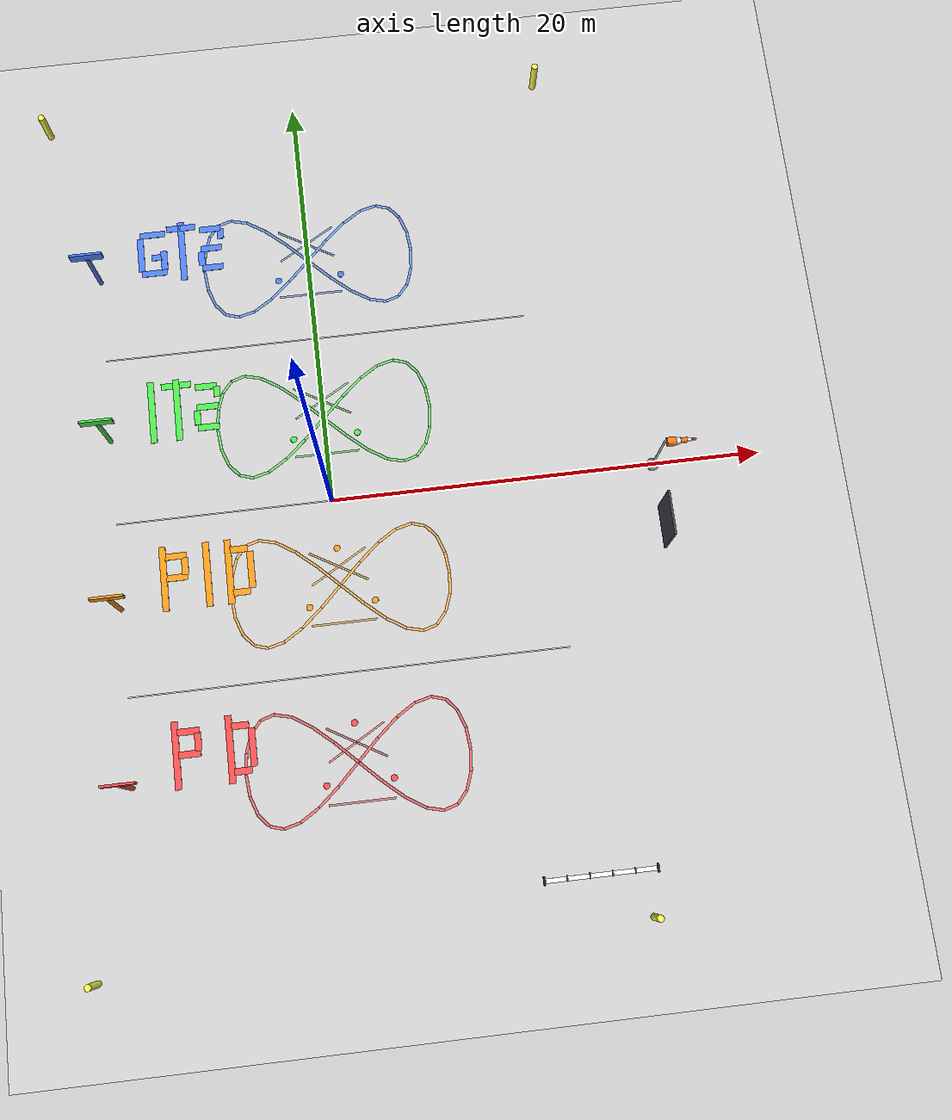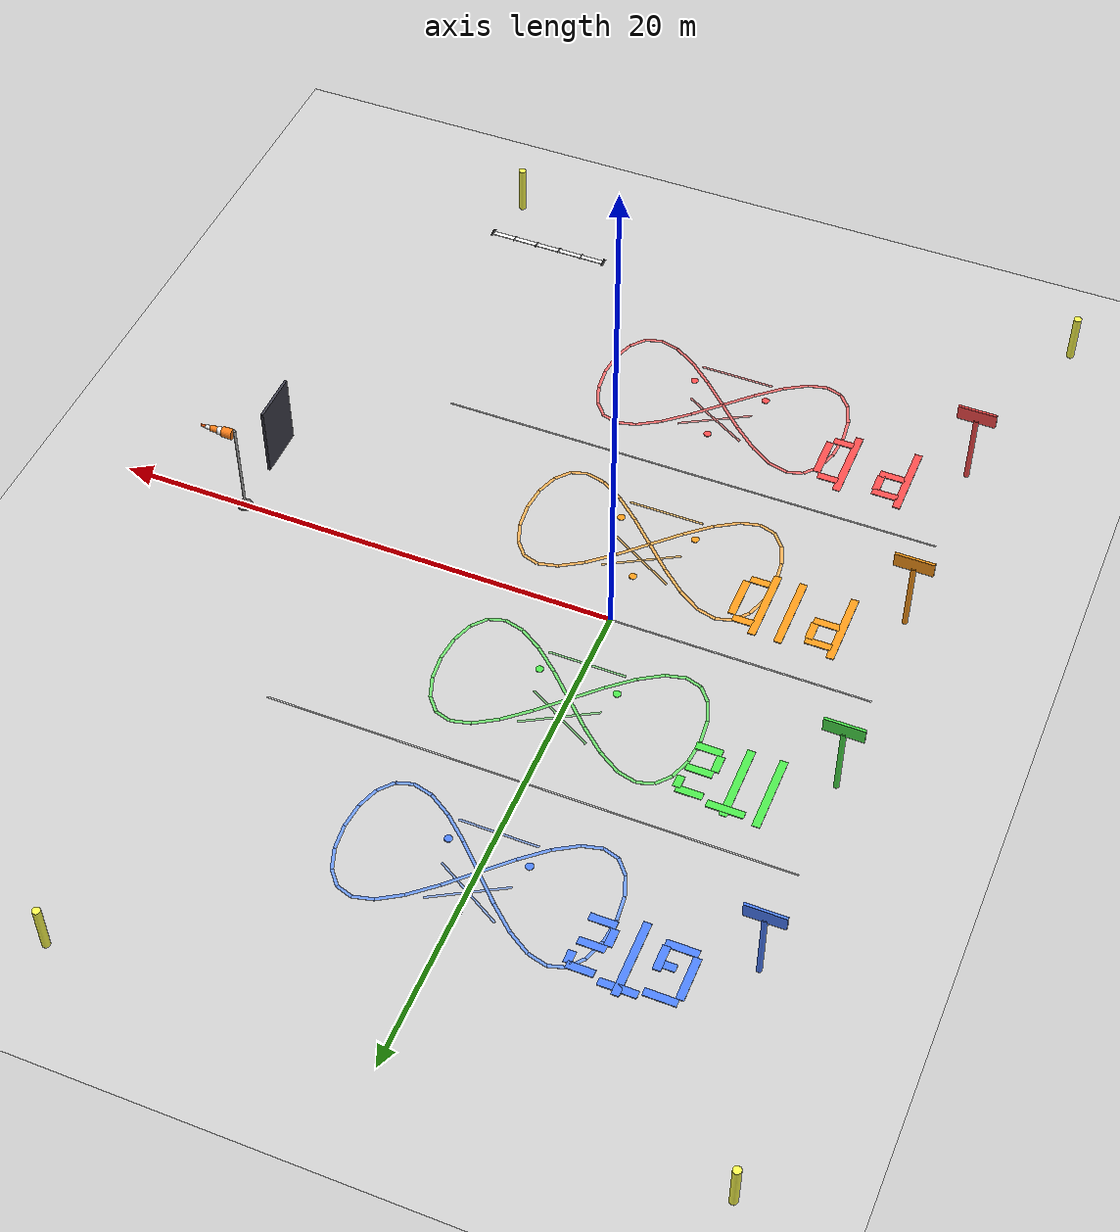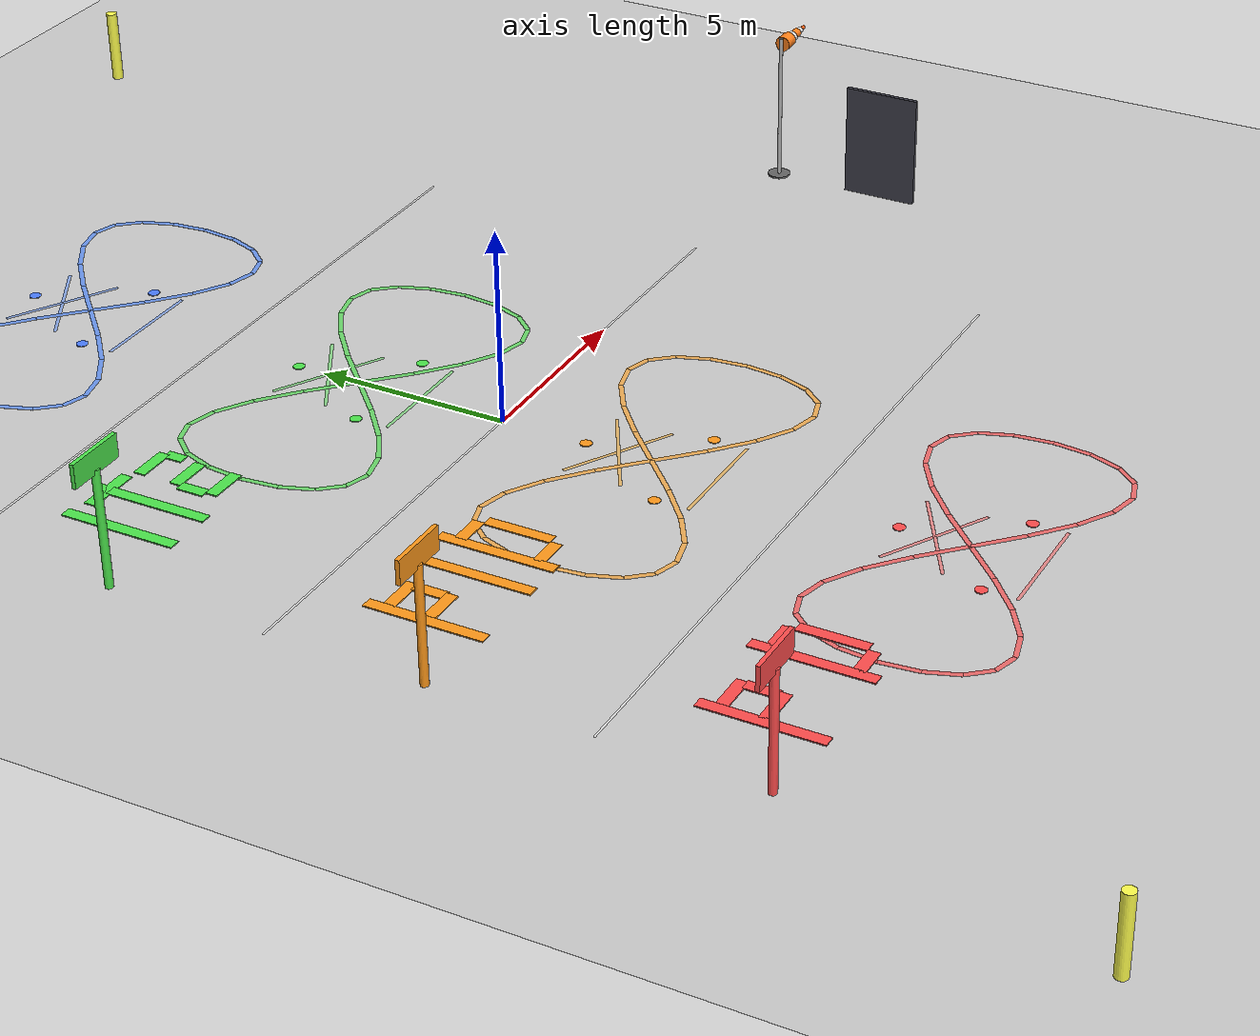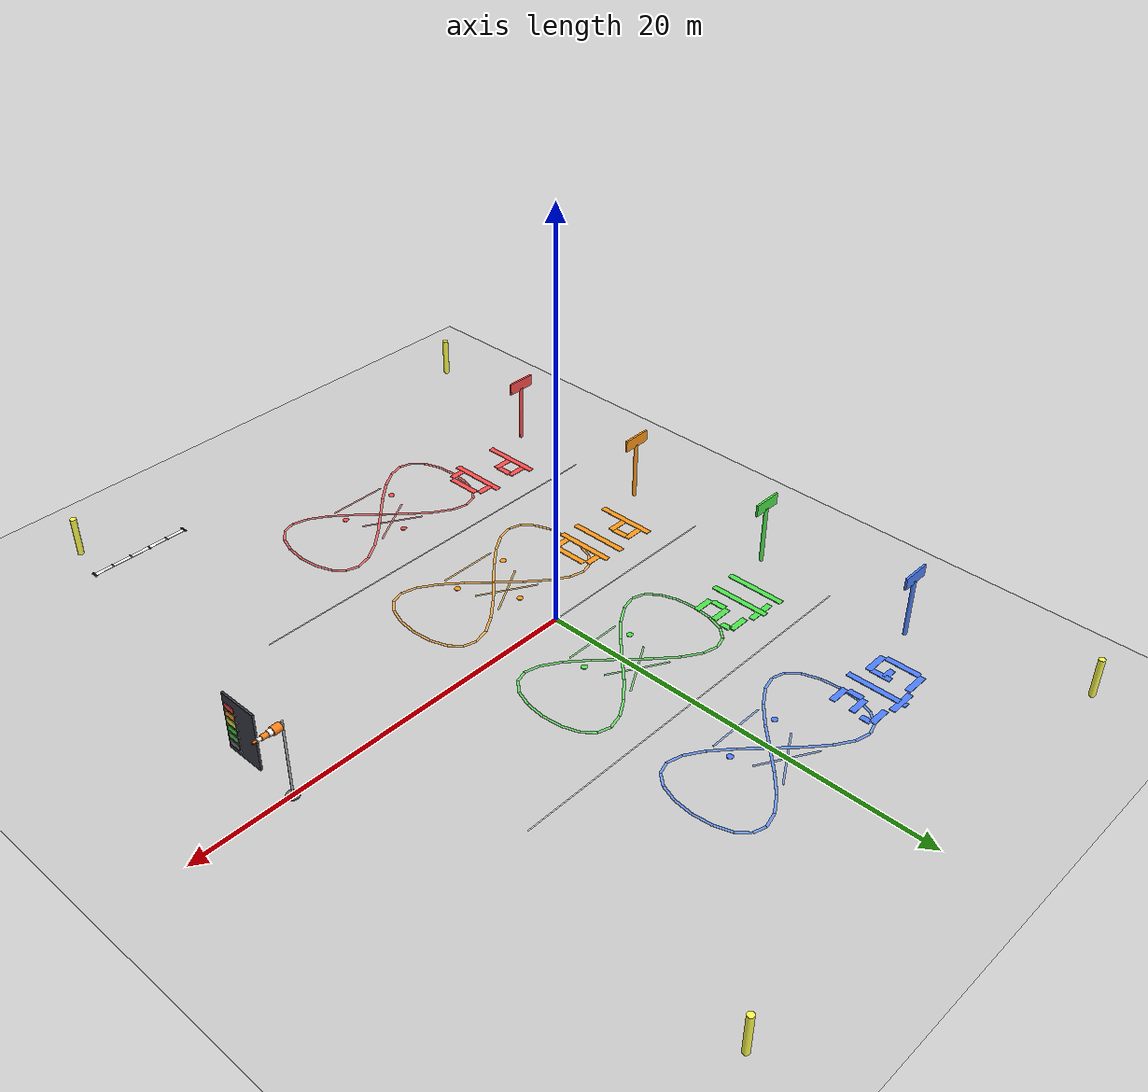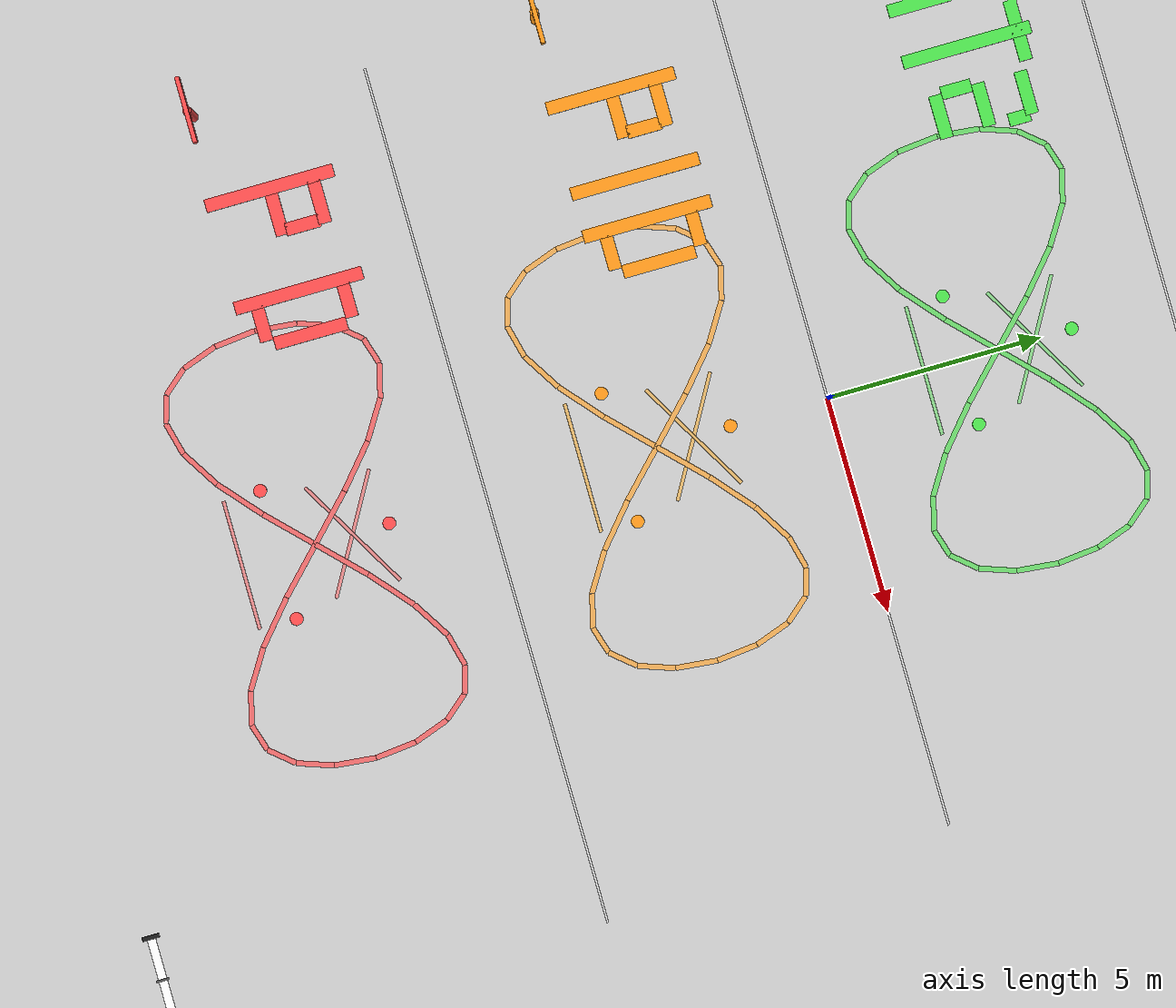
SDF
<sdf version="1.6">
 <world name="professional_formation_arena">
  <physics type="ode">
   <max_step_size>0.001</max_step_size>
   <real_time_factor>1.0</real_time_factor>
   <real_time_update_rate>1000</real_time_update_rate>
   <ode>
    <solver><type>quick</type><iters>50</iters><sor>1.3</sor></solver>
    <constraints>
     <cfm>0.0</cfm>
     <erp>0.2</erp>
     <contact_max_correcting_vel>100</contact_max_correcting_vel>
     <contact_surface_layer>0.001</contact_surface_layer>
    </constraints>
   </ode>
  </physics>
  <plugin name="gazebo_ros_init" filename="libgazebo_ros_init.so"><ros><namespace>/</namespace></ros></plugin>
  <plugin name="gazebo_ros_properties" filename="libgazebo_ros_properties.so">
   <ros><namespace>/</namespace></ros>
  </plugin>
  <light name="sun" type="directional">
   <pose>0 0 50 0 0 0</pose>
   <diffuse>0.9 0.9 0.9 1</diffuse>
   <specular>0.2 0.2 0.2 1</specular>
   <attenuation>
    <range>1000</range>
    <constant>0.9</constant>
    <linear>0.01</linear>
    <quadratic>0.001</quadratic>
   </attenuation>
   <direction>-0.3 0.4 -1.0</direction>
  </light>
  <light name="ambient" type="point">
   <pose>0 0 30 0 0 0</pose>
   <diffuse>0.3 0.3 0.35 1</diffuse>
   <specular>0.1 0.1 0.1 1</specular>
   <attenuation>
    <range>200</range>
    <constant>0.3</constant>
    <linear>0.01</linear>
    <quadratic>0.001</quadratic>
   </attenuation>
  </light>
  <scene><ambient>0.4 0.4 0.45 1</ambient><background>0.5 0.6 0.8 1</background><shadows>true</shadows></scene>
  <include><uri>model://arena_ground</uri></include>
  <model name="wind_indicator">
   <static>false</static>
   <pose>15 0 0 0 0 0</pose>
   <link name="base">
    <inertial>
     <mass>100</mass>
     <inertia><ixx>100</ixx><iyy>100</iyy><izz>100</izz><ixy>0</ixy><ixz>0</ixz><iyz>0</iyz></inertia>
    </inertial>
    <visual name="pole">
     <pose>0 0 2 0 0 0</pose>
     <geometry><cylinder><radius>0.05</radius><length>4.0</length></cylinder></geometry>
     <material><ambient>0.6 0.6 0.6 1</ambient><diffuse>0.7 0.7 0.7 1</diffuse></material>
    </visual>
    <visual name="base_plate">
     <pose>0 0 0.025 0 0 0</pose>
     <geometry><cylinder><radius>0.3</radius><length>0.05</length></cylinder></geometry>
     <material><ambient>0.3 0.3 0.3 1</ambient><diffuse>0.4 0.4 0.4 1</diffuse></material>
    </visual>
    <collision name="base_collision">
     <pose>0 0 0.025 0 0 0</pose>
     <geometry><cylinder><radius>0.3</radius><length>0.05</length></cylinder></geometry>
    </collision>
   </link>
   <link name="flag">
    <pose>0 0 3.8 0 0 0</pose>
    <inertial>
     <mass>0.5</mass>
     <inertia><ixx>0.01</ixx><iyy>0.1</iyy><izz>0.1</izz><ixy>0</ixy><ixz>0</ixz><iyz>0</iyz></inertia>
    </inertial>
    <visual name="sock_1">
     <pose>0.3 0 0 0 1.5708 0</pose>
     <geometry><cylinder><radius>0.2</radius><length>0.4</length></cylinder></geometry>
     <material><ambient>1 0.4 0 1</ambient><diffuse>1 0.5 0.1 1</diffuse></material>
    </visual>
    <visual name="sock_2">
     <pose>0.6 0 0 0 1.5708 0</pose>
     <geometry><cylinder><radius>0.15</radius><length>0.2</length></cylinder></geometry>
     <material><ambient>1 1 1 1</ambient><diffuse>1 1 1 1</diffuse></material>
    </visual>
    <visual name="sock_3">
     <pose>0.85 0 0 0 1.5708 0</pose>
     <geometry><cylinder><radius>0.12</radius><length>0.3</length></cylinder></geometry>
     <material><ambient>1 0.4 0 1</ambient><diffuse>1 0.5 0.1 1</diffuse></material>
    </visual>
    <visual name="sock_4">
     <pose>1.1 0 0 0 1.5708 0</pose>
     <geometry><cylinder><radius>0.08</radius><length>0.2</length></cylinder></geometry>
     <material><ambient>1 1 1 1</ambient><diffuse>1 1 1 1</diffuse></material>
    </visual>
    <visual name="sock_tip">
     <pose>1.3 0 0 0 1.5708 0</pose>
     <geometry><cylinder><radius>0.05</radius><length>0.2</length></cylinder></geometry>
     <material><ambient>1 0.3 0 1</ambient><diffuse>1 0.4 0.1 1</diffuse></material>
    </visual>
   </link>
   <joint name="flag_joint" type="revolute">
    <parent>base</parent>
    <child>flag</child>
    <axis>
     <xyz>0 0 1</xyz>
     <limit><lower>-3.15</lower><upper>3.15</upper></limit>
     <dynamics><damping>0.5</damping></dynamics>
    </axis>
   </joint>
   <plugin name="wind_flag_plugin" filename="libwind_flag_plugin.so">
    <joint_name>flag_joint</joint_name>
    <wind_topic>/wind/velocity</wind_topic>
    <update_rate>10</update_rate>
   </plugin>
  </model>
  <model name="traj_pd">
   <static>true</static>
   <link name="path">
    <visual name="seg0">
     <pose>0.488 -11.522 0.015 0 0 0.7757</pose>
     <geometry><box><size>1.366 0.12 0.015</size></box></geometry>
     <material><ambient>1 0.3 0.3 0.85</ambient><diffuse>1 0.4 0.4 0.85</diffuse></material>
    </visual>
    <visual name="seg1">
     <pose>1.444 -10.638 0.015 0 0 0.7130</pose>
     <geometry><box><size>1.240 0.12 0.015</size></box></geometry>
     <material><ambient>1 0.3 0.3 0.85</ambient><diffuse>1 0.4 0.4 0.85</diffuse></material>
    </visual>
    <visual name="seg2">
     <pose>2.346 -9.961 0.015 0 0 0.5600</pose>
     <geometry><box><size>1.020 0.12 0.015</size></box></geometry>
     <material><ambient>1 0.3 0.3 0.85</ambient><diffuse>1 0.4 0.4 0.85</diffuse></material>
    </visual>
    <visual name="seg3">
     <pose>3.157 -9.595 0.015 0 0 0.2461</pose>
     <geometry><box><size>0.781 0.12 0.015</size></box></geometry>
     <material><ambient>1 0.3 0.3 0.85</ambient><diffuse>1 0.4 0.4 0.85</diffuse></material>
    </visual>
    <visual name="seg4">
     <pose>3.846 -9.595 0.015 0 0 -0.2970</pose>
     <geometry><box><size>0.650 0.12 0.015</size></box></geometry>
     <material><ambient>1 0.3 0.3 0.85</ambient><diffuse>1 0.4 0.4 0.85</diffuse></material>
    </visual>
    <visual name="seg5">
     <pose>4.388 -9.961 0.015 0 0 -0.8648</pose>
     <geometry><box><size>0.712 0.12 0.015</size></box></geometry>
     <material><ambient>1 0.3 0.3 0.85</ambient><diffuse>1 0.4 0.4 0.85</diffuse></material>
    </visual>
    <visual name="seg6">
     <pose>4.762 -10.638 0.015 0 0 -1.2334</pose>
     <geometry><box><size>0.860 0.12 0.015</size></box></geometry>
     <material><ambient>1 0.3 0.3 0.85</ambient><diffuse>1 0.4 0.4 0.85</diffuse></material>
    </visual>
    <visual name="seg7">
     <pose>4.952 -11.522 0.015 0 0 -1.4707</pose>
     <geometry><box><size>0.962 0.12 0.015</size></box></geometry>
     <material><ambient>1 0.3 0.3 0.85</ambient><diffuse>1 0.4 0.4 0.85</diffuse></material>
    </visual>
    <visual name="seg8">
     <pose>4.952 -12.478 0.015 0 0 -1.6709</pose>
     <geometry><box><size>0.962 0.12 0.015</size></box></geometry>
     <material><ambient>1 0.3 0.3 0.85</ambient><diffuse>1 0.4 0.4 0.85</diffuse></material>
    </visual>
    <visual name="seg9">
     <pose>4.762 -13.362 0.015 0 0 -1.9082</pose>
     <geometry><box><size>0.860 0.12 0.015</size></box></geometry>
     <material><ambient>1 0.3 0.3 0.85</ambient><diffuse>1 0.4 0.4 0.85</diffuse></material>
    </visual>
    <visual name="seg10">
     <pose>4.388 -14.039 0.015 0 0 -2.2768</pose>
     <geometry><box><size>0.712 0.12 0.015</size></box></geometry>
     <material><ambient>1 0.3 0.3 0.85</ambient><diffuse>1 0.4 0.4 0.85</diffuse></material>
    </visual>
    <visual name="seg11">
     <pose>3.846 -14.405 0.015 0 0 -2.8446</pose>
     <geometry><box><size>0.650 0.12 0.015</size></box></geometry>
     <material><ambient>1 0.3 0.3 0.85</ambient><diffuse>1 0.4 0.4 0.85</diffuse></material>
    </visual>
    <visual name="seg12">
     <pose>3.157 -14.405 0.015 0 0 2.8955</pose>
     <geometry><box><size>0.781 0.12 0.015</size></box></geometry>
     <material><ambient>1 0.3 0.3 0.85</ambient><diffuse>1 0.4 0.4 0.85</diffuse></material>
    </visual>
    <visual name="seg13">
     <pose>2.346 -14.039 0.015 0 0 2.5816</pose>
     <geometry><box><size>1.020 0.12 0.015</size></box></geometry>
     <material><ambient>1 0.3 0.3 0.85</ambient><diffuse>1 0.4 0.4 0.85</diffuse></material>
    </visual>
    <visual name="seg14">
     <pose>1.444 -13.362 0.015 0 0 2.4286</pose>
     <geometry><box><size>1.240 0.12 0.015</size></box></geometry>
     <material><ambient>1 0.3 0.3 0.85</ambient><diffuse>1 0.4 0.4 0.85</diffuse></material>
    </visual>
    <visual name="seg15">
     <pose>0.488 -12.478 0.015 0 0 2.3659</pose>
     <geometry><box><size>1.366 0.12 0.015</size></box></geometry>
     <material><ambient>1 0.3 0.3 0.85</ambient><diffuse>1 0.4 0.4 0.85</diffuse></material>
    </visual>
    <visual name="seg16">
     <pose>-0.488 -11.522 0.015 0 0 2.3659</pose>
     <geometry><box><size>1.366 0.12 0.015</size></box></geometry>
     <material><ambient>1 0.3 0.3 0.85</ambient><diffuse>1 0.4 0.4 0.85</diffuse></material>
    </visual>
    <visual name="seg17">
     <pose>-1.444 -10.638 0.015 0 0 2.4286</pose>
     <geometry><box><size>1.240 0.12 0.015</size></box></geometry>
     <material><ambient>1 0.3 0.3 0.85</ambient><diffuse>1 0.4 0.4 0.85</diffuse></material>
    </visual>
    <visual name="seg18">
     <pose>-2.346 -9.961 0.015 0 0 2.5816</pose>
     <geometry><box><size>1.020 0.12 0.015</size></box></geometry>
     <material><ambient>1 0.3 0.3 0.85</ambient><diffuse>1 0.4 0.4 0.85</diffuse></material>
    </visual>
    <visual name="seg19">
     <pose>-3.157 -9.595 0.015 0 0 2.8955</pose>
     <geometry><box><size>0.781 0.12 0.015</size></box></geometry>
     <material><ambient>1 0.3 0.3 0.85</ambient><diffuse>1 0.4 0.4 0.85</diffuse></material>
    </visual>
    <visual name="seg20">
     <pose>-3.846 -9.595 0.015 0 0 -2.8446</pose>
     <geometry><box><size>0.650 0.12 0.015</size></box></geometry>
     <material><ambient>1 0.3 0.3 0.85</ambient><diffuse>1 0.4 0.4 0.85</diffuse></material>
    </visual>
    <visual name="seg21">
     <pose>-4.388 -9.961 0.015 0 0 -2.2768</pose>
     <geometry><box><size>0.712 0.12 0.015</size></box></geometry>
     <material><ambient>1 0.3 0.3 0.85</ambient><diffuse>1 0.4 0.4 0.85</diffuse></material>
    </visual>
    <visual name="seg22">
     <pose>-4.762 -10.638 0.015 0 0 -1.9082</pose>
     <geometry><box><size>0.860 0.12 0.015</size></box></geometry>
     <material><ambient>1 0.3 0.3 0.85</ambient><diffuse>1 0.4 0.4 0.85</diffuse></material>
    </visual>
    <visual name="seg23">
     <pose>-4.952 -11.522 0.015 0 0 -1.6709</pose>
     <geometry><box><size>0.962 0.12 0.015</size></box></geometry>
     <material><ambient>1 0.3 0.3 0.85</ambient><diffuse>1 0.4 0.4 0.85</diffuse></material>
    </visual>
    <visual name="seg24">
     <pose>-4.952 -12.478 0.015 0 0 -1.4707</pose>
     <geometry><box><size>0.962 0.12 0.015</size></box></geometry>
     <material><ambient>1 0.3 0.3 0.85</ambient><diffuse>1 0.4 0.4 0.85</diffuse></material>
    </visual>
    <visual name="seg25">
     <pose>-4.762 -13.362 0.015 0 0 -1.2334</pose>
     <geometry><box><size>0.860 0.12 0.015</size></box></geometry>
     <material><ambient>1 0.3 0.3 0.85</ambient><diffuse>1 0.4 0.4 0.85</diffuse></material>
    </visual>
    <visual name="seg26">
     <pose>-4.388 -14.039 0.015 0 0 -0.8648</pose>
     <geometry><box><size>0.712 0.12 0.015</size></box></geometry>
     <material><ambient>1 0.3 0.3 0.85</ambient><diffuse>1 0.4 0.4 0.85</diffuse></material>
    </visual>
    <visual name="seg27">
     <pose>-3.846 -14.405 0.015 0 0 -0.2970</pose>
     <geometry><box><size>0.650 0.12 0.015</size></box></geometry>
     <material><ambient>1 0.3 0.3 0.85</ambient><diffuse>1 0.4 0.4 0.85</diffuse></material>
    </visual>
    <visual name="seg28">
     <pose>-3.157 -14.405 0.015 0 0 0.2461</pose>
     <geometry><box><size>0.781 0.12 0.015</size></box></geometry>
     <material><ambient>1 0.3 0.3 0.85</ambient><diffuse>1 0.4 0.4 0.85</diffuse></material>
    </visual>
    <visual name="seg29">
     <pose>-2.346 -14.039 0.015 0 0 0.5600</pose>
     <geometry><box><size>1.020 0.12 0.015</size></box></geometry>
     <material><ambient>1 0.3 0.3 0.85</ambient><diffuse>1 0.4 0.4 0.85</diffuse></material>
    </visual>
    <visual name="seg30">
     <pose>-1.444 -13.362 0.015 0 0 0.7130</pose>
     <geometry><box><size>1.240 0.12 0.015</size></box></geometry>
     <material><ambient>1 0.3 0.3 0.85</ambient><diffuse>1 0.4 0.4 0.85</diffuse></material>
    </visual>
    <visual name="seg31">
     <pose>-0.488 -12.478 0.015 0 0 0.7757</pose>
     <geometry><box><size>1.366 0.12 0.015</size></box></geometry>
     <material><ambient>1 0.3 0.3 0.85</ambient><diffuse>1 0.4 0.4 0.85</diffuse></material>
    </visual>
   </link>
  </model>
  <model name="traj_pid">
   <static>true</static>
   <link name="path">
    <visual name="seg0">
     <pose>0.488 -3.522 0.015 0 0 0.7757</pose>
     <geometry><box><size>1.366 0.12 0.015</size></box></geometry>
     <material><ambient>1 0.6 0.2 0.85</ambient><diffuse>1 0.7 0.3 0.85</diffuse></material>
    </visual>
    <visual name="seg1">
     <pose>1.444 -2.638 0.015 0 0 0.7130</pose>
     <geometry><box><size>1.240 0.12 0.015</size></box></geometry>
     <material><ambient>1 0.6 0.2 0.85</ambient><diffuse>1 0.7 0.3 0.85</diffuse></material>
    </visual>
    <visual name="seg2">
     <pose>2.346 -1.961 0.015 0 0 0.5600</pose>
     <geometry><box><size>1.020 0.12 0.015</size></box></geometry>
     <material><ambient>1 0.6 0.2 0.85</ambient><diffuse>1 0.7 0.3 0.85</diffuse></material>
    </visual>
    <visual name="seg3">
     <pose>3.157 -1.595 0.015 0 0 0.2461</pose>
     <geometry><box><size>0.781 0.12 0.015</size></box></geometry>
     <material><ambient>1 0.6 0.2 0.85</ambient><diffuse>1 0.7 0.3 0.85</diffuse></material>
    </visual>
    <visual name="seg4">
     <pose>3.846 -1.595 0.015 0 0 -0.2970</pose>
     <geometry><box><size>0.650 0.12 0.015</size></box></geometry>
     <material><ambient>1 0.6 0.2 0.85</ambient><diffuse>1 0.7 0.3 0.85</diffuse></material>
    </visual>
    <visual name="seg5">
     <pose>4.388 -1.961 0.015 0 0 -0.8648</pose>
     <geometry><box><size>0.712 0.12 0.015</size></box></geometry>
     <material><ambient>1 0.6 0.2 0.85</ambient><diffuse>1 0.7 0.3 0.85</diffuse></material>
    </visual>
    <visual name="seg6">
     <pose>4.762 -2.638 0.015 0 0 -1.2334</pose>
     <geometry><box><size>0.860 0.12 0.015</size></box></geometry>
     <material><ambient>1 0.6 0.2 0.85</ambient><diffuse>1 0.7 0.3 0.85</diffuse></material>
    </visual>
    <visual name="seg7">
     <pose>4.952 -3.522 0.015 0 0 -1.4707</pose>
     <geometry><box><size>0.962 0.12 0.015</size></box></geometry>
     <material><ambient>1 0.6 0.2 0.85</ambient><diffuse>1 0.7 0.3 0.85</diffuse></material>
    </visual>
    <visual name="seg8">
     <pose>4.952 -4.478 0.015 0 0 -1.6709</pose>
     <geometry><box><size>0.962 0.12 0.015</size></box></geometry>
     <material><ambient>1 0.6 0.2 0.85</ambient><diffuse>1 0.7 0.3 0.85</diffuse></material>
    </visual>
    <visual name="seg9">
     <pose>4.762 -5.362 0.015 0 0 -1.9082</pose>
     <geometry><box><size>0.860 0.12 0.015</size></box></geometry>
     <material><ambient>1 0.6 0.2 0.85</ambient><diffuse>1 0.7 0.3 0.85</diffuse></material>
    </visual>
    <visual name="seg10">
     <pose>4.388 -6.039 0.015 0 0 -2.2768</pose>
     <geometry><box><size>0.712 0.12 0.015</size></box></geometry>
     <material><ambient>1 0.6 0.2 0.85</ambient><diffuse>1 0.7 0.3 0.85</diffuse></material>
    </visual>
    <visual name="seg11">
     <pose>3.846 -6.405 0.015 0 0 -2.8446</pose>
     <geometry><box><size>0.650 0.12 0.015</size></box></geometry>
     <material><ambient>1 0.6 0.2 0.85</ambient><diffuse>1 0.7 0.3 0.85</diffuse></material>
    </visual>
    <visual name="seg12">
     <pose>3.157 -6.405 0.015 0 0 2.8955</pose>
     <geometry><box><size>0.781 0.12 0.015</size></box></geometry>
     <material><ambient>1 0.6 0.2 0.85</ambient><diffuse>1 0.7 0.3 0.85</diffuse></material>
    </visual>
    <visual name="seg13">
     <pose>2.346 -6.039 0.015 0 0 2.5816</pose>
     <geometry><box><size>1.020 0.12 0.015</size></box></geometry>
     <material><ambient>1 0.6 0.2 0.85</ambient><diffuse>1 0.7 0.3 0.85</diffuse></material>
    </visual>
    <visual name="seg14">
     <pose>1.444 -5.362 0.015 0 0 2.4286</pose>
     <geometry><box><size>1.240 0.12 0.015</size></box></geometry>
     <material><ambient>1 0.6 0.2 0.85</ambient><diffuse>1 0.7 0.3 0.85</diffuse></material>
    </visual>
    <visual name="seg15">
     <pose>0.488 -4.478 0.015 0 0 2.3659</pose>
     <geometry><box><size>1.366 0.12 0.015</size></box></geometry>
     <material><ambient>1 0.6 0.2 0.85</ambient><diffuse>1 0.7 0.3 0.85</diffuse></material>
    </visual>
    <visual name="seg16">
     <pose>-0.488 -3.522 0.015 0 0 2.3659</pose>
     <geometry><box><size>1.366 0.12 0.015</size></box></geometry>
     <material><ambient>1 0.6 0.2 0.85</ambient><diffuse>1 0.7 0.3 0.85</diffuse></material>
    </visual>
    <visual name="seg17">
     <pose>-1.444 -2.638 0.015 0 0 2.4286</pose>
     <geometry><box><size>1.240 0.12 0.015</size></box></geometry>
     <material><ambient>1 0.6 0.2 0.85</ambient><diffuse>1 0.7 0.3 0.85</diffuse></material>
    </visual>
    <visual name="seg18">
     <pose>-2.346 -1.961 0.015 0 0 2.5816</pose>
     <geometry><box><size>1.020 0.12 0.015</size></box></geometry>
     <material><ambient>1 0.6 0.2 0.85</ambient><diffuse>1 0.7 0.3 0.85</diffuse></material>
    </visual>
    <visual name="seg19">
     <pose>-3.157 -1.595 0.015 0 0 2.8955</pose>
     <geometry><box><size>0.781 0.12 0.015</size></box></geometry>
     <material><ambient>1 0.6 0.2 0.85</ambient><diffuse>1 0.7 0.3 0.85</diffuse></material>
    </visual>
    <visual name="seg20">
     <pose>-3.846 -1.595 0.015 0 0 -2.8446</pose>
     <geometry><box><size>0.650 0.12 0.015</size></box></geometry>
     <material><ambient>1 0.6 0.2 0.85</ambient><diffuse>1 0.7 0.3 0.85</diffuse></material>
    </visual>
    <visual name="seg21">
     <pose>-4.388 -1.961 0.015 0 0 -2.2768</pose>
     <geometry><box><size>0.712 0.12 0.015</size></box></geometry>
     <material><ambient>1 0.6 0.2 0.85</ambient><diffuse>1 0.7 0.3 0.85</diffuse></material>
    </visual>
    <visual name="seg22">
     <pose>-4.762 -2.638 0.015 0 0 -1.9082</pose>
     <geometry><box><size>0.860 0.12 0.015</size></box></geometry>
     <material><ambient>1 0.6 0.2 0.85</ambient><diffuse>1 0.7 0.3 0.85</diffuse></material>
    </visual>
    <visual name="seg23">
     <pose>-4.952 -3.522 0.015 0 0 -1.6709</pose>
     <geometry><box><size>0.962 0.12 0.015</size></box></geometry>
     <material><ambient>1 0.6 0.2 0.85</ambient><diffuse>1 0.7 0.3 0.85</diffuse></material>
    </visual>
    <visual name="seg24">
     <pose>-4.952 -4.478 0.015 0 0 -1.4707</pose>
     <geometry><box><size>0.962 0.12 0.015</size></box></geometry>
     <material><ambient>1 0.6 0.2 0.85</ambient><diffuse>1 0.7 0.3 0.85</diffuse></material>
    </visual>
    <visual name="seg25">
     <pose>-4.762 -5.362 0.015 0 0 -1.2334</pose>
     <geometry><box><size>0.860 0.12 0.015</size></box></geometry>
     <material><ambient>1 0.6 0.2 0.85</ambient><diffuse>1 0.7 0.3 0.85</diffuse></material>
    </visual>
    <visual name="seg26">
     <pose>-4.388 -6.039 0.015 0 0 -0.8648</pose>
     <geometry><box><size>0.712 0.12 0.015</size></box></geometry>
     <material><ambient>1 0.6 0.2 0.85</ambient><diffuse>1 0.7 0.3 0.85</diffuse></material>
    </visual>
    <visual name="seg27">
     <pose>-3.846 -6.405 0.015 0 0 -0.2970</pose>
     <geometry><box><size>0.650 0.12 0.015</size></box></geometry>
     <material><ambient>1 0.6 0.2 0.85</ambient><diffuse>1 0.7 0.3 0.85</diffuse></material>
    </visual>
    <visual name="seg28">
     <pose>-3.157 -6.405 0.015 0 0 0.2461</pose>
     <geometry><box><size>0.781 0.12 0.015</size></box></geometry>
     <material><ambient>1 0.6 0.2 0.85</ambient><diffuse>1 0.7 0.3 0.85</diffuse></material>
    </visual>
    <visual name="seg29">
     <pose>-2.346 -6.039 0.015 0 0 0.5600</pose>
     <geometry><box><size>1.020 0.12 0.015</size></box></geometry>
     <material><ambient>1 0.6 0.2 0.85</ambient><diffuse>1 0.7 0.3 0.85</diffuse></material>
    </visual>
    <visual name="seg30">
     <pose>-1.444 -5.362 0.015 0 0 0.7130</pose>
     <geometry><box><size>1.240 0.12 0.015</size></box></geometry>
     <material><ambient>1 0.6 0.2 0.85</ambient><diffuse>1 0.7 0.3 0.85</diffuse></material>
    </visual>
    <visual name="seg31">
     <pose>-0.488 -4.478 0.015 0 0 0.7757</pose>
     <geometry><box><size>1.366 0.12 0.015</size></box></geometry>
     <material><ambient>1 0.6 0.2 0.85</ambient><diffuse>1 0.7 0.3 0.85</diffuse></material>
    </visual>
   </link>
  </model>
  <model name="traj_it2">
   <static>true</static>
   <link name="path">
    <visual name="seg0">
     <pose>0.488 4.478 0.015 0 0 0.7757</pose>
     <geometry><box><size>1.366 0.12 0.015</size></box></geometry>
     <material><ambient>0.3 0.85 0.3 0.85</ambient><diffuse>0.4 0.9 0.4 0.85</diffuse></material>
    </visual>
    <visual name="seg1">
     <pose>1.444 5.362 0.015 0 0 0.7130</pose>
     <geometry><box><size>1.240 0.12 0.015</size></box></geometry>
     <material><ambient>0.3 0.85 0.3 0.85</ambient><diffuse>0.4 0.9 0.4 0.85</diffuse></material>
    </visual>
    <visual name="seg2">
     <pose>2.346 6.039 0.015 0 0 0.5600</pose>
     <geometry><box><size>1.020 0.12 0.015</size></box></geometry>
     <material><ambient>0.3 0.85 0.3 0.85</ambient><diffuse>0.4 0.9 0.4 0.85</diffuse></material>
    </visual>
    <visual name="seg3">
     <pose>3.157 6.405 0.015 0 0 0.2461</pose>
     <geometry><box><size>0.781 0.12 0.015</size></box></geometry>
     <material><ambient>0.3 0.85 0.3 0.85</ambient><diffuse>0.4 0.9 0.4 0.85</diffuse></material>
    </visual>
    <visual name="seg4">
     <pose>3.846 6.405 0.015 0 0 -0.2970</pose>
     <geometry><box><size>0.650 0.12 0.015</size></box></geometry>
     <material><ambient>0.3 0.85 0.3 0.85</ambient><diffuse>0.4 0.9 0.4 0.85</diffuse></material>
    </visual>
    <visual name="seg5">
     <pose>4.388 6.039 0.015 0 0 -0.8648</pose>
     <geometry><box><size>0.712 0.12 0.015</size></box></geometry>
     <material><ambient>0.3 0.85 0.3 0.85</ambient><diffuse>0.4 0.9 0.4 0.85</diffuse></material>
    </visual>
    <visual name="seg6">
     <pose>4.762 5.362 0.015 0 0 -1.2334</pose>
     <geometry><box><size>0.860 0.12 0.015</size></box></geometry>
     <material><ambient>0.3 0.85 0.3 0.85</ambient><diffuse>0.4 0.9 0.4 0.85</diffuse></material>
    </visual>
    <visual name="seg7">
     <pose>4.952 4.478 0.015 0 0 -1.4707</pose>
     <geometry><box><size>0.962 0.12 0.015</size></box></geometry>
     <material><ambient>0.3 0.85 0.3 0.85</ambient><diffuse>0.4 0.9 0.4 0.85</diffuse></material>
    </visual>
    <visual name="seg8">
     <pose>4.952 3.522 0.015 0 0 -1.6709</pose>
     <geometry><box><size>0.962 0.12 0.015</size></box></geometry>
     <material><ambient>0.3 0.85 0.3 0.85</ambient><diffuse>0.4 0.9 0.4 0.85</diffuse></material>
    </visual>
    <visual name="seg9">
     <pose>4.762 2.638 0.015 0 0 -1.9082</pose>
     <geometry><box><size>0.860 0.12 0.015</size></box></geometry>
     <material><ambient>0.3 0.85 0.3 0.85</ambient><diffuse>0.4 0.9 0.4 0.85</diffuse></material>
    </visual>
    <visual name="seg10">
     <pose>4.388 1.961 0.015 0 0 -2.2768</pose>
     <geometry><box><size>0.712 0.12 0.015</size></box></geometry>
     <material><ambient>0.3 0.85 0.3 0.85</ambient><diffuse>0.4 0.9 0.4 0.85</diffuse></material>
    </visual>
    <visual name="seg11">
     <pose>3.846 1.595 0.015 0 0 -2.8446</pose>
     <geometry><box><size>0.650 0.12 0.015</size></box></geometry>
     <material><ambient>0.3 0.85 0.3 0.85</ambient><diffuse>0.4 0.9 0.4 0.85</diffuse></material>
    </visual>
    <visual name="seg12">
     <pose>3.157 1.595 0.015 0 0 2.8955</pose>
     <geometry><box><size>0.781 0.12 0.015</size></box></geometry>
     <material><ambient>0.3 0.85 0.3 0.85</ambient><diffuse>0.4 0.9 0.4 0.85</diffuse></material>
    </visual>
    <visual name="seg13">
     <pose>2.346 1.961 0.015 0 0 2.5816</pose>
     <geometry><box><size>1.020 0.12 0.015</size></box></geometry>
     <material><ambient>0.3 0.85 0.3 0.85</ambient><diffuse>0.4 0.9 0.4 0.85</diffuse></material>
    </visual>
    <visual name="seg14">
     <pose>1.444 2.638 0.015 0 0 2.4286</pose>
     <geometry><box><size>1.240 0.12 0.015</size></box></geometry>
     <material><ambient>0.3 0.85 0.3 0.85</ambient><diffuse>0.4 0.9 0.4 0.85</diffuse></material>
    </visual>
    <visual name="seg15">
     <pose>0.488 3.522 0.015 0 0 2.3659</pose>
     <geometry><box><size>1.366 0.12 0.015</size></box></geometry>
     <material><ambient>0.3 0.85 0.3 0.85</ambient><diffuse>0.4 0.9 0.4 0.85</diffuse></material>
    </visual>
    <visual name="seg16">
     <pose>-0.488 4.478 0.015 0 0 2.3659</pose>
     <geometry><box><size>1.366 0.12 0.015</size></box></geometry>
     <material><ambient>0.3 0.85 0.3 0.85</ambient><diffuse>0.4 0.9 0.4 0.85</diffuse></material>
    </visual>
    <visual name="seg17">
     <pose>-1.444 5.362 0.015 0 0 2.4286</pose>
     <geometry><box><size>1.240 0.12 0.015</size></box></geometry>
     <material><ambient>0.3 0.85 0.3 0.85</ambient><diffuse>0.4 0.9 0.4 0.85</diffuse></material>
    </visual>
    <visual name="seg18">
     <pose>-2.346 6.039 0.015 0 0 2.5816</pose>
     <geometry><box><size>1.020 0.12 0.015</size></box></geometry>
     <material><ambient>0.3 0.85 0.3 0.85</ambient><diffuse>0.4 0.9 0.4 0.85</diffuse></material>
    </visual>
    <visual name="seg19">
     <pose>-3.157 6.405 0.015 0 0 2.8955</pose>
     <geometry><box><size>0.781 0.12 0.015</size></box></geometry>
     <material><ambient>0.3 0.85 0.3 0.85</ambient><diffuse>0.4 0.9 0.4 0.85</diffuse></material>
    </visual>
    <visual name="seg20">
     <pose>-3.846 6.405 0.015 0 0 -2.8446</pose>
     <geometry><box><size>0.650 0.12 0.015</size></box></geometry>
     <material><ambient>0.3 0.85 0.3 0.85</ambient><diffuse>0.4 0.9 0.4 0.85</diffuse></material>
    </visual>
    <visual name="seg21">
     <pose>-4.388 6.039 0.015 0 0 -2.2768</pose>
     <geometry><box><size>0.712 0.12 0.015</size></box></geometry>
     <material><ambient>0.3 0.85 0.3 0.85</ambient><diffuse>0.4 0.9 0.4 0.85</diffuse></material>
    </visual>
    <visual name="seg22">
     <pose>-4.762 5.362 0.015 0 0 -1.9082</pose>
     <geometry><box><size>0.860 0.12 0.015</size></box></geometry>
     <material><ambient>0.3 0.85 0.3 0.85</ambient><diffuse>0.4 0.9 0.4 0.85</diffuse></material>
    </visual>
    <visual name="seg23">
     <pose>-4.952 4.478 0.015 0 0 -1.6709</pose>
     <geometry><box><size>0.962 0.12 0.015</size></box></geometry>
     <material><ambient>0.3 0.85 0.3 0.85</ambient><diffuse>0.4 0.9 0.4 0.85</diffuse></material>
    </visual>
    <visual name="seg24">
     <pose>-4.952 3.522 0.015 0 0 -1.4707</pose>
     <geometry><box><size>0.962 0.12 0.015</size></box></geometry>
     <material><ambient>0.3 0.85 0.3 0.85</ambient><diffuse>0.4 0.9 0.4 0.85</diffuse></material>
    </visual>
    <visual name="seg25">
     <pose>-4.762 2.638 0.015 0 0 -1.2334</pose>
     <geometry><box><size>0.860 0.12 0.015</size></box></geometry>
     <material><ambient>0.3 0.85 0.3 0.85</ambient><diffuse>0.4 0.9 0.4 0.85</diffuse></material>
    </visual>
    <visual name="seg26">
     <pose>-4.388 1.961 0.015 0 0 -0.8648</pose>
     <geometry><box><size>0.712 0.12 0.015</size></box></geometry>
     <material><ambient>0.3 0.85 0.3 0.85</ambient><diffuse>0.4 0.9 0.4 0.85</diffuse></material>
    </visual>
    <visual name="seg27">
     <pose>-3.846 1.595 0.015 0 0 -0.2970</pose>
     <geometry><box><size>0.650 0.12 0.015</size></box></geometry>
     <material><ambient>0.3 0.85 0.3 0.85</ambient><diffuse>0.4 0.9 0.4 0.85</diffuse></material>
    </visual>
    <visual name="seg28">
     <pose>-3.157 1.595 0.015 0 0 0.2461</pose>
     <geometry><box><size>0.781 0.12 0.015</size></box></geometry>
     <material><ambient>0.3 0.85 0.3 0.85</ambient><diffuse>0.4 0.9 0.4 0.85</diffuse></material>
    </visual>
    <visual name="seg29">
     <pose>-2.346 1.961 0.015 0 0 0.5600</pose>
     <geometry><box><size>1.020 0.12 0.015</size></box></geometry>
     <material><ambient>0.3 0.85 0.3 0.85</ambient><diffuse>0.4 0.9 0.4 0.85</diffuse></material>
    </visual>
    <visual name="seg30">
     <pose>-1.444 2.638 0.015 0 0 0.7130</pose>
     <geometry><box><size>1.240 0.12 0.015</size></box></geometry>
     <material><ambient>0.3 0.85 0.3 0.85</ambient><diffuse>0.4 0.9 0.4 0.85</diffuse></material>
    </visual>
    <visual name="seg31">
     <pose>-0.488 3.522 0.015 0 0 0.7757</pose>
     <geometry><box><size>1.366 0.12 0.015</size></box></geometry>
     <material><ambient>0.3 0.85 0.3 0.85</ambient><diffuse>0.4 0.9 0.4 0.85</diffuse></material>
    </visual>
   </link>
  </model>
  <model name="traj_gt2">
   <static>true</static>
   <link name="path">
    <visual name="seg0">
     <pose>0.488 12.478 0.015 0 0 0.7757</pose>
     <geometry><box><size>1.366 0.12 0.015</size></box></geometry>
     <material><ambient>0.3 0.5 1 0.85</ambient><diffuse>0.4 0.6 1 0.85</diffuse></material>
    </visual>
    <visual name="seg1">
     <pose>1.444 13.362 0.015 0 0 0.7130</pose>
     <geometry><box><size>1.240 0.12 0.015</size></box></geometry>
     <material><ambient>0.3 0.5 1 0.85</ambient><diffuse>0.4 0.6 1 0.85</diffuse></material>
    </visual>
    <visual name="seg2">
     <pose>2.346 14.039 0.015 0 0 0.5600</pose>
     <geometry><box><size>1.020 0.12 0.015</size></box></geometry>
     <material><ambient>0.3 0.5 1 0.85</ambient><diffuse>0.4 0.6 1 0.85</diffuse></material>
    </visual>
    <visual name="seg3">
     <pose>3.157 14.405 0.015 0 0 0.2461</pose>
     <geometry><box><size>0.781 0.12 0.015</size></box></geometry>
     <material><ambient>0.3 0.5 1 0.85</ambient><diffuse>0.4 0.6 1 0.85</diffuse></material>
    </visual>
    <visual name="seg4">
     <pose>3.846 14.405 0.015 0 0 -0.2970</pose>
     <geometry><box><size>0.650 0.12 0.015</size></box></geometry>
     <material><ambient>0.3 0.5 1 0.85</ambient><diffuse>0.4 0.6 1 0.85</diffuse></material>
    </visual>
    <visual name="seg5">
     <pose>4.388 14.039 0.015 0 0 -0.8648</pose>
     <geometry><box><size>0.712 0.12 0.015</size></box></geometry>
     <material><ambient>0.3 0.5 1 0.85</ambient><diffuse>0.4 0.6 1 0.85</diffuse></material>
    </visual>
    <visual name="seg6">
     <pose>4.762 13.362 0.015 0 0 -1.2334</pose>
     <geometry><box><size>0.860 0.12 0.015</size></box></geometry>
     <material><ambient>0.3 0.5 1 0.85</ambient><diffuse>0.4 0.6 1 0.85</diffuse></material>
    </visual>
    <visual name="seg7">
     <pose>4.952 12.478 0.015 0 0 -1.4707</pose>
     <geometry><box><size>0.962 0.12 0.015</size></box></geometry>
     <material><ambient>0.3 0.5 1 0.85</ambient><diffuse>0.4 0.6 1 0.85</diffuse></material>
    </visual>
    <visual name="seg8">
     <pose>4.952 11.522 0.015 0 0 -1.6709</pose>
     <geometry><box><size>0.962 0.12 0.015</size></box></geometry>
     <material><ambient>0.3 0.5 1 0.85</ambient><diffuse>0.4 0.6 1 0.85</diffuse></material>
    </visual>
    <visual name="seg9">
     <pose>4.762 10.638 0.015 0 0 -1.9082</pose>
     <geometry><box><size>0.860 0.12 0.015</size></box></geometry>
     <material><ambient>0.3 0.5 1 0.85</ambient><diffuse>0.4 0.6 1 0.85</diffuse></material>
    </visual>
    <visual name="seg10">
     <pose>4.388 9.961 0.015 0 0 -2.2768</pose>
     <geometry><box><size>0.712 0.12 0.015</size></box></geometry>
     <material><ambient>0.3 0.5 1 0.85</ambient><diffuse>0.4 0.6 1 0.85</diffuse></material>
    </visual>
    <visual name="seg11">
     <pose>3.846 9.595 0.015 0 0 -2.8446</pose>
     <geometry><box><size>0.650 0.12 0.015</size></box></geometry>
     <material><ambient>0.3 0.5 1 0.85</ambient><diffuse>0.4 0.6 1 0.85</diffuse></material>
    </visual>
    <visual name="seg12">
     <pose>3.157 9.595 0.015 0 0 2.8955</pose>
     <geometry><box><size>0.781 0.12 0.015</size></box></geometry>
     <material><ambient>0.3 0.5 1 0.85</ambient><diffuse>0.4 0.6 1 0.85</diffuse></material>
    </visual>
    <visual name="seg13">
     <pose>2.346 9.961 0.015 0 0 2.5816</pose>
     <geometry><box><size>1.020 0.12 0.015</size></box></geometry>
     <material><ambient>0.3 0.5 1 0.85</ambient><diffuse>0.4 0.6 1 0.85</diffuse></material>
    </visual>
    <visual name="seg14">
     <pose>1.444 10.638 0.015 0 0 2.4286</pose>
     <geometry><box><size>1.240 0.12 0.015</size></box></geometry>
     <material><ambient>0.3 0.5 1 0.85</ambient><diffuse>0.4 0.6 1 0.85</diffuse></material>
    </visual>
    <visual name="seg15">
     <pose>0.488 11.522 0.015 0 0 2.3659</pose>
     <geometry><box><size>1.366 0.12 0.015</size></box></geometry>
     <material><ambient>0.3 0.5 1 0.85</ambient><diffuse>0.4 0.6 1 0.85</diffuse></material>
    </visual>
    <visual name="seg16">
     <pose>-0.488 12.478 0.015 0 0 2.3659</pose>
     <geometry><box><size>1.366 0.12 0.015</size></box></geometry>
     <material><ambient>0.3 0.5 1 0.85</ambient><diffuse>0.4 0.6 1 0.85</diffuse></material>
    </visual>
    <visual name="seg17">
     <pose>-1.444 13.362 0.015 0 0 2.4286</pose>
     <geometry><box><size>1.240 0.12 0.015</size></box></geometry>
     <material><ambient>0.3 0.5 1 0.85</ambient><diffuse>0.4 0.6 1 0.85</diffuse></material>
    </visual>
    <visual name="seg18">
     <pose>-2.346 14.039 0.015 0 0 2.5816</pose>
     <geometry><box><size>1.020 0.12 0.015</size></box></geometry>
     <material><ambient>0.3 0.5 1 0.85</ambient><diffuse>0.4 0.6 1 0.85</diffuse></material>
    </visual>
    <visual name="seg19">
     <pose>-3.157 14.405 0.015 0 0 2.8955</pose>
     <geometry><box><size>0.781 0.12 0.015</size></box></geometry>
     <material><ambient>0.3 0.5 1 0.85</ambient><diffuse>0.4 0.6 1 0.85</diffuse></material>
    </visual>
    <visual name="seg20">
     <pose>-3.846 14.405 0.015 0 0 -2.8446</pose>
     <geometry><box><size>0.650 0.12 0.015</size></box></geometry>
     <material><ambient>0.3 0.5 1 0.85</ambient><diffuse>0.4 0.6 1 0.85</diffuse></material>
    </visual>
    <visual name="seg21">
     <pose>-4.388 14.039 0.015 0 0 -2.2768</pose>
     <geometry><box><size>0.712 0.12 0.015</size></box></geometry>
     <material><ambient>0.3 0.5 1 0.85</ambient><diffuse>0.4 0.6 1 0.85</diffuse></material>
    </visual>
    <visual name="seg22">
     <pose>-4.762 13.362 0.015 0 0 -1.9082</pose>
     <geometry><box><size>0.860 0.12 0.015</size></box></geometry>
     <material><ambient>0.3 0.5 1 0.85</ambient><diffuse>0.4 0.6 1 0.85</diffuse></material>
    </visual>
    <visual name="seg23">
     <pose>-4.952 12.478 0.015 0 0 -1.6709</pose>
     <geometry><box><size>0.962 0.12 0.015</size></box></geometry>
     <material><ambient>0.3 0.5 1 0.85</ambient><diffuse>0.4 0.6 1 0.85</diffuse></material>
    </visual>
    <visual name="seg24">
     <pose>-4.952 11.522 0.015 0 0 -1.4707</pose>
     <geometry><box><size>0.962 0.12 0.015</size></box></geometry>
     <material><ambient>0.3 0.5 1 0.85</ambient><diffuse>0.4 0.6 1 0.85</diffuse></material>
    </visual>
    <visual name="seg25">
     <pose>-4.762 10.638 0.015 0 0 -1.2334</pose>
     <geometry><box><size>0.860 0.12 0.015</size></box></geometry>
     <material><ambient>0.3 0.5 1 0.85</ambient><diffuse>0.4 0.6 1 0.85</diffuse></material>
    </visual>
    <visual name="seg26">
     <pose>-4.388 9.961 0.015 0 0 -0.8648</pose>
     <geometry><box><size>0.712 0.12 0.015</size></box></geometry>
     <material><ambient>0.3 0.5 1 0.85</ambient><diffuse>0.4 0.6 1 0.85</diffuse></material>
    </visual>
    <visual name="seg27">
     <pose>-3.846 9.595 0.015 0 0 -0.2970</pose>
     <geometry><box><size>0.650 0.12 0.015</size></box></geometry>
     <material><ambient>0.3 0.5 1 0.85</ambient><diffuse>0.4 0.6 1 0.85</diffuse></material>
    </visual>
    <visual name="seg28">
     <pose>-3.157 9.595 0.015 0 0 0.2461</pose>
     <geometry><box><size>0.781 0.12 0.015</size></box></geometry>
     <material><ambient>0.3 0.5 1 0.85</ambient><diffuse>0.4 0.6 1 0.85</diffuse></material>
    </visual>
    <visual name="seg29">
     <pose>-2.346 9.961 0.015 0 0 0.5600</pose>
     <geometry><box><size>1.020 0.12 0.015</size></box></geometry>
     <material><ambient>0.3 0.5 1 0.85</ambient><diffuse>0.4 0.6 1 0.85</diffuse></material>
    </visual>
    <visual name="seg30">
     <pose>-1.444 10.638 0.015 0 0 0.7130</pose>
     <geometry><box><size>1.240 0.12 0.015</size></box></geometry>
     <material><ambient>0.3 0.5 1 0.85</ambient><diffuse>0.4 0.6 1 0.85</diffuse></material>
    </visual>
    <visual name="seg31">
     <pose>-0.488 11.522 0.015 0 0 0.7757</pose>
     <geometry><box><size>1.366 0.12 0.015</size></box></geometry>
     <material><ambient>0.3 0.5 1 0.85</ambient><diffuse>0.4 0.6 1 0.85</diffuse></material>
    </visual>
   </link>
  </model>
  <model name="post_pd">
   <static>true</static>
   <pose>-10 -12 0 0 0 0</pose>
   <link name="link">
    <visual name="pole">
     <pose>0 0 1.5 0 0 0</pose>
     <geometry><cylinder><radius>0.1</radius><length>3.0</length></cylinder></geometry>
     <material><ambient>1 0.2 0.2 1</ambient><diffuse>1 0.3 0.3 1</diffuse></material>
    </visual>
    <visual name="sign">
     <pose>0 0 3.2 0 0 0</pose>
     <geometry><box><size>1.5 0.1 0.6</size></box></geometry>
     <material><ambient>1 0.2 0.2 1</ambient><diffuse>1 0.3 0.3 1</diffuse></material>
    </visual>
   </link>
  </model>
  <model name="post_pid">
   <static>true</static>
   <pose>-10 -4 0 0 0 0</pose>
   <link name="link">
    <visual name="pole">
     <pose>0 0 1.5 0 0 0</pose>
     <geometry><cylinder><radius>0.1</radius><length>3.0</length></cylinder></geometry>
     <material><ambient>1 0.5 0 1</ambient><diffuse>1 0.6 0.1 1</diffuse></material>
    </visual>
    <visual name="sign">
     <pose>0 0 3.2 0 0 0</pose>
     <geometry><box><size>1.5 0.1 0.6</size></box></geometry>
     <material><ambient>1 0.5 0 1</ambient><diffuse>1 0.6 0.1 1</diffuse></material>
    </visual>
   </link>
  </model>
  <model name="post_it2">
   <static>true</static>
   <pose>-10 4 0 0 0 0</pose>
   <link name="link">
    <visual name="pole">
     <pose>0 0 1.5 0 0 0</pose>
     <geometry><cylinder><radius>0.1</radius><length>3.0</length></cylinder></geometry>
     <material><ambient>0.2 0.8 0.2 1</ambient><diffuse>0.3 0.9 0.3 1</diffuse></material>
    </visual>
    <visual name="sign">
     <pose>0 0 3.2 0 0 0</pose>
     <geometry><box><size>1.5 0.1 0.6</size></box></geometry>
     <material><ambient>0.2 0.8 0.2 1</ambient><diffuse>0.3 0.9 0.3 1</diffuse></material>
    </visual>
   </link>
  </model>
  <model name="post_gt2">
   <static>true</static>
   <pose>-10 12 0 0 0 0</pose>
   <link name="link">
    <visual name="pole">
     <pose>0 0 1.5 0 0 0</pose>
     <geometry><cylinder><radius>0.1</radius><length>3.0</length></cylinder></geometry>
     <material><ambient>0.2 0.4 1 1</ambient><diffuse>0.3 0.5 1 1</diffuse></material>
    </visual>
    <visual name="sign">
     <pose>0 0 3.2 0 0 0</pose>
     <geometry><box><size>1.5 0.1 0.6</size></box></geometry>
     <material><ambient>0.2 0.4 1 1</ambient><diffuse>0.3 0.5 1 1</diffuse></material>
    </visual>
   </link>
  </model>
  <model name="corner_nw">
   <static>true</static>
   <pose>-12 20 0 0 0 0</pose>
   <link name="link">
    <visual name="v">
     <pose>0 0 1 0 0 0</pose>
     <geometry><cylinder><radius>0.15</radius><length>2.0</length></cylinder></geometry>
     <material><ambient>0.9 0.9 0.2 1</ambient><diffuse>1 1 0.3 1</diffuse></material>
    </visual>
   </link>
  </model>
  <model name="corner_ne">
   <static>true</static>
   <pose>12 20 0 0 0 0</pose>
   <link name="link">
    <visual name="v">
     <pose>0 0 1 0 0 0</pose>
     <geometry><cylinder><radius>0.15</radius><length>2.0</length></cylinder></geometry>
     <material><ambient>0.9 0.9 0.2 1</ambient><diffuse>1 1 0.3 1</diffuse></material>
    </visual>
   </link>
  </model>
  <model name="corner_sw">
   <static>true</static>
   <pose>-12 -20 0 0 0 0</pose>
   <link name="link">
    <visual name="v">
     <pose>0 0 1 0 0 0</pose>
     <geometry><cylinder><radius>0.15</radius><length>2.0</length></cylinder></geometry>
     <material><ambient>0.9 0.9 0.2 1</ambient><diffuse>1 1 0.3 1</diffuse></material>
    </visual>
   </link>
  </model>
  <model name="corner_se">
   <static>true</static>
   <pose>12 -20 0 0 0 0</pose>
   <link name="link">
    <visual name="v">
     <pose>0 0 1 0 0 0</pose>
     <geometry><cylinder><radius>0.15</radius><length>2.0</length></cylinder></geometry>
     <material><ambient>0.9 0.9 0.2 1</ambient><diffuse>1 1 0.3 1</diffuse></material>
    </visual>
   </link>
  </model>
  <model name="lane_lines">
   <static>true</static>
   <link name="link">
    <visual name="line1">
     <pose>0 -8 0.01 0 0 0</pose>
     <geometry><box><size>20 0.05 0.01</size></box></geometry>
     <material><ambient>1 1 1 0.5</ambient><diffuse>1 1 1 0.5</diffuse></material>
    </visual>
    <visual name="line2">
     <pose>0 0 0.01 0 0 0</pose>
     <geometry><box><size>20 0.05 0.01</size></box></geometry>
     <material><ambient>1 1 1 0.5</ambient><diffuse>1 1 1 0.5</diffuse></material>
    </visual>
    <visual name="line3">
     <pose>0 8 0.01 0 0 0</pose>
     <geometry><box><size>20 0.05 0.01</size></box></geometry>
     <material><ambient>1 1 1 0.5</ambient><diffuse>1 1 1 0.5</diffuse></material>
    </visual>
   </link>
  </model>
  <model name="scale_bar">
   <static>true</static>
   <pose>10 -18 0 0 0 0</pose>
   <link name="link">
    <visual name="bar">
     <pose>0 0 0.02 0 0 0</pose>
     <geometry><box><size>5.0 0.2 0.02</size></box></geometry>
     <material><ambient>1 1 1 1</ambient><diffuse>1 1 1 1</diffuse></material>
    </visual>
    <visual name="mark_0">
     <pose>-2.5 0 0.03 0 0 0</pose>
     <geometry><box><size>0.1 0.4 0.02</size></box></geometry>
     <material><ambient>0 0 0 1</ambient><diffuse>0.1 0.1 0.1 1</diffuse></material>
    </visual>
    <visual name="mark_5">
     <pose>2.5 0 0.03 0 0 0</pose>
     <geometry><box><size>0.1 0.4 0.02</size></box></geometry>
     <material><ambient>0 0 0 1</ambient><diffuse>0.1 0.1 0.1 1</diffuse></material>
    </visual>
    <visual name="mark_1">
     <pose>-1.5 0 0.025 0 0 0</pose>
     <geometry><box><size>0.05 0.3 0.02</size></box></geometry>
     <material><ambient>0.3 0.3 0.3 1</ambient><diffuse>0.3 0.3 0.3 1</diffuse></material>
    </visual>
    <visual name="mark_2">
     <pose>-0.5 0 0.025 0 0 0</pose>
     <geometry><box><size>0.05 0.3 0.02</size></box></geometry>
     <material><ambient>0.3 0.3 0.3 1</ambient><diffuse>0.3 0.3 0.3 1</diffuse></material>
    </visual>
    <visual name="mark_3">
     <pose>0.5 0 0.025 0 0 0</pose>
     <geometry><box><size>0.05 0.3 0.02</size></box></geometry>
     <material><ambient>0.3 0.3 0.3 1</ambient><diffuse>0.3 0.3 0.3 1</diffuse></material>
    </visual>
    <visual name="mark_4">
     <pose>1.5 0 0.025 0 0 0</pose>
     <geometry><box><size>0.05 0.3 0.02</size></box></geometry>
     <material><ambient>0.3 0.3 0.3 1</ambient><diffuse>0.3 0.3 0.3 1</diffuse></material>
    </visual>
   </link>
  </model>
  <model name="label_ground_pd">
   <static>true</static>
   <pose>-8 -12 0.02 0 0 0</pose>
   <link name="link">
    <visual name="p1">
     <pose>0 1.2 0 0 0 0</pose>
     <geometry><box><size>0.3 3.0 0.03</size></box></geometry>
     <material><ambient>1 0.2 0.2 1</ambient><diffuse>1 0.3 0.3 1</diffuse></material>
    </visual>
    <visual name="p2">
     <pose>0.6 2.2 0 0 0 0</pose>
     <geometry><box><size>1.0 0.3 0.03</size></box></geometry>
     <material><ambient>1 0.2 0.2 1</ambient><diffuse>1 0.3 0.3 1</diffuse></material>
    </visual>
    <visual name="p3">
     <pose>1.0 1.7 0 0 0 0</pose>
     <geometry><box><size>0.3 0.8 0.03</size></box></geometry>
     <material><ambient>1 0.2 0.2 1</ambient><diffuse>1 0.3 0.3 1</diffuse></material>
    </visual>
    <visual name="p4">
     <pose>0.6 1.2 0 0 0 0</pose>
     <geometry><box><size>1.0 0.3 0.03</size></box></geometry>
     <material><ambient>1 0.2 0.2 1</ambient><diffuse>1 0.3 0.3 1</diffuse></material>
    </visual>
    <visual name="d1">
     <pose>2.4 1.2 0 0 0 0</pose>
     <geometry><box><size>0.3 3.0 0.03</size></box></geometry>
     <material><ambient>1 0.2 0.2 1</ambient><diffuse>1 0.3 0.3 1</diffuse></material>
    </visual>
    <visual name="d2">
     <pose>2.9 2.2 0 0 0 0</pose>
     <geometry><box><size>0.8 0.3 0.03</size></box></geometry>
     <material><ambient>1 0.2 0.2 1</ambient><diffuse>1 0.3 0.3 1</diffuse></material>
    </visual>
    <visual name="d3">
     <pose>2.9 0.2 0 0 0 0</pose>
     <geometry><box><size>0.8 0.3 0.03</size></box></geometry>
     <material><ambient>1 0.2 0.2 1</ambient><diffuse>1 0.3 0.3 1</diffuse></material>
    </visual>
    <visual name="d4">
     <pose>3.4 1.2 0 0 0 0</pose>
     <geometry><box><size>0.3 1.7 0.03</size></box></geometry>
     <material><ambient>1 0.2 0.2 1</ambient><diffuse>1 0.3 0.3 1</diffuse></material>
    </visual>
   </link>
  </model>
  <model name="label_ground_pid">
   <static>true</static>
   <pose>-8 -4 0.02 0 0 0</pose>
   <link name="link">
    <visual name="p1">
     <pose>0 1.2 0 0 0 0</pose>
     <geometry><box><size>0.3 3.0 0.03</size></box></geometry>
     <material><ambient>1 0.5 0 1</ambient><diffuse>1 0.6 0.1 1</diffuse></material>
    </visual>
    <visual name="p2">
     <pose>0.6 2.2 0 0 0 0</pose>
     <geometry><box><size>1.0 0.3 0.03</size></box></geometry>
     <material><ambient>1 0.5 0 1</ambient><diffuse>1 0.6 0.1 1</diffuse></material>
    </visual>
    <visual name="p3">
     <pose>1.0 1.7 0 0 0 0</pose>
     <geometry><box><size>0.3 0.8 0.03</size></box></geometry>
     <material><ambient>1 0.5 0 1</ambient><diffuse>1 0.6 0.1 1</diffuse></material>
    </visual>
    <visual name="p4">
     <pose>0.6 1.2 0 0 0 0</pose>
     <geometry><box><size>1.0 0.3 0.03</size></box></geometry>
     <material><ambient>1 0.5 0 1</ambient><diffuse>1 0.6 0.1 1</diffuse></material>
    </visual>
    <visual name="i1">
     <pose>2.0 1.2 0 0 0 0</pose>
     <geometry><box><size>0.3 3.0 0.03</size></box></geometry>
     <material><ambient>1 0.5 0 1</ambient><diffuse>1 0.6 0.1 1</diffuse></material>
    </visual>
    <visual name="d1">
     <pose>3.0 1.2 0 0 0 0</pose>
     <geometry><box><size>0.3 3.0 0.03</size></box></geometry>
     <material><ambient>1 0.5 0 1</ambient><diffuse>1 0.6 0.1 1</diffuse></material>
    </visual>
    <visual name="d2">
     <pose>3.5 2.2 0 0 0 0</pose>
     <geometry><box><size>0.8 0.3 0.03</size></box></geometry>
     <material><ambient>1 0.5 0 1</ambient><diffuse>1 0.6 0.1 1</diffuse></material>
    </visual>
    <visual name="d3">
     <pose>3.5 0.2 0 0 0 0</pose>
     <geometry><box><size>0.8 0.3 0.03</size></box></geometry>
     <material><ambient>1 0.5 0 1</ambient><diffuse>1 0.6 0.1 1</diffuse></material>
    </visual>
    <visual name="d4">
     <pose>4.0 1.2 0 0 0 0</pose>
     <geometry><box><size>0.3 1.7 0.03</size></box></geometry>
     <material><ambient>1 0.5 0 1</ambient><diffuse>1 0.6 0.1 1</diffuse></material>
    </visual>
   </link>
  </model>
  <model name="label_ground_it2">
   <static>true</static>
   <pose>-8 4 0.02 0 0 0</pose>
   <link name="link">
    <visual name="i1">
     <pose>0 1.2 0 0 0 0</pose>
     <geometry><box><size>0.3 3.0 0.03</size></box></geometry>
     <material><ambient>0.2 0.8 0.2 1</ambient><diffuse>0.3 0.9 0.3 1</diffuse></material>
    </visual>
    <visual name="t1">
     <pose>1.2 1.2 0 0 0 0</pose>
     <geometry><box><size>0.3 3.0 0.03</size></box></geometry>
     <material><ambient>0.2 0.8 0.2 1</ambient><diffuse>0.3 0.9 0.3 1</diffuse></material>
    </visual>
    <visual name="t2">
     <pose>1.2 2.4 0 0 0 0</pose>
     <geometry><box><size>1.4 0.3 0.03</size></box></geometry>
     <material><ambient>0.2 0.8 0.2 1</ambient><diffuse>0.3 0.9 0.3 1</diffuse></material>
    </visual>
    <visual name="n1">
     <pose>2.6 2.2 0 0 0 0</pose>
     <geometry><box><size>1.0 0.3 0.03</size></box></geometry>
     <material><ambient>0.2 0.8 0.2 1</ambient><diffuse>0.3 0.9 0.3 1</diffuse></material>
    </visual>
    <visual name="n2">
     <pose>3.1 1.9 0 0 0 0</pose>
     <geometry><box><size>0.3 0.5 0.03</size></box></geometry>
     <material><ambient>0.2 0.8 0.2 1</ambient><diffuse>0.3 0.9 0.3 1</diffuse></material>
    </visual>
    <visual name="n3">
     <pose>2.6 1.2 0 0 0 0</pose>
     <geometry><box><size>1.0 0.3 0.03</size></box></geometry>
     <material><ambient>0.2 0.8 0.2 1</ambient><diffuse>0.3 0.9 0.3 1</diffuse></material>
    </visual>
    <visual name="n4">
     <pose>2.1 0.7 0 0 0 0</pose>
     <geometry><box><size>0.3 0.7 0.03</size></box></geometry>
     <material><ambient>0.2 0.8 0.2 1</ambient><diffuse>0.3 0.9 0.3 1</diffuse></material>
    </visual>
    <visual name="n5">
     <pose>2.6 0.2 0 0 0 0</pose>
     <geometry><box><size>1.0 0.3 0.03</size></box></geometry>
     <material><ambient>0.2 0.8 0.2 1</ambient><diffuse>0.3 0.9 0.3 1</diffuse></material>
    </visual>
   </link>
  </model>
  <model name="label_ground_gt2">
   <static>true</static>
   <pose>-8 12 0.02 0 0 0</pose>
   <link name="link">
    <visual name="g1">
     <pose>0.6 2.2 0 0 0 0</pose>
     <geometry><box><size>1.2 0.3 0.03</size></box></geometry>
     <material><ambient>0.2 0.4 1 1</ambient><diffuse>0.3 0.5 1 1</diffuse></material>
    </visual>
    <visual name="g2">
     <pose>0 1.2 0 0 0 0</pose>
     <geometry><box><size>0.3 1.7 0.03</size></box></geometry>
     <material><ambient>0.2 0.4 1 1</ambient><diffuse>0.3 0.5 1 1</diffuse></material>
    </visual>
    <visual name="g3">
     <pose>0.6 0.2 0 0 0 0</pose>
     <geometry><box><size>1.2 0.3 0.03</size></box></geometry>
     <material><ambient>0.2 0.4 1 1</ambient><diffuse>0.3 0.5 1 1</diffuse></material>
    </visual>
    <visual name="g4">
     <pose>1.1 0.8 0 0 0 0</pose>
     <geometry><box><size>0.3 1.0 0.03</size></box></geometry>
     <material><ambient>0.2 0.4 1 1</ambient><diffuse>0.3 0.5 1 1</diffuse></material>
    </visual>
    <visual name="g5">
     <pose>0.8 1.0 0 0 0 0</pose>
     <geometry><box><size>0.6 0.3 0.03</size></box></geometry>
     <material><ambient>0.2 0.4 1 1</ambient><diffuse>0.3 0.5 1 1</diffuse></material>
    </visual>
    <visual name="t1">
     <pose>2.0 1.2 0 0 0 0</pose>
     <geometry><box><size>0.3 3.0 0.03</size></box></geometry>
     <material><ambient>0.2 0.4 1 1</ambient><diffuse>0.3 0.5 1 1</diffuse></material>
    </visual>
    <visual name="t2">
     <pose>2.0 2.4 0 0 0 0</pose>
     <geometry><box><size>1.4 0.3 0.03</size></box></geometry>
     <material><ambient>0.2 0.4 1 1</ambient><diffuse>0.3 0.5 1 1</diffuse></material>
    </visual>
    <visual name="n1">
     <pose>3.4 2.2 0 0 0 0</pose>
     <geometry><box><size>1.0 0.3 0.03</size></box></geometry>
     <material><ambient>0.2 0.4 1 1</ambient><diffuse>0.3 0.5 1 1</diffuse></material>
    </visual>
    <visual name="n2">
     <pose>3.9 1.9 0 0 0 0</pose>
     <geometry><box><size>0.3 0.5 0.03</size></box></geometry>
     <material><ambient>0.2 0.4 1 1</ambient><diffuse>0.3 0.5 1 1</diffuse></material>
    </visual>
    <visual name="n3">
     <pose>3.4 1.2 0 0 0 0</pose>
     <geometry><box><size>1.0 0.3 0.03</size></box></geometry>
     <material><ambient>0.2 0.4 1 1</ambient><diffuse>0.3 0.5 1 1</diffuse></material>
    </visual>
    <visual name="n4">
     <pose>2.9 0.7 0 0 0 0</pose>
     <geometry><box><size>0.3 0.7 0.03</size></box></geometry>
     <material><ambient>0.2 0.4 1 1</ambient><diffuse>0.3 0.5 1 1</diffuse></material>
    </visual>
    <visual name="n5">
     <pose>3.4 0.2 0 0 0 0</pose>
     <geometry><box><size>1.0 0.3 0.03</size></box></geometry>
     <material><ambient>0.2 0.4 1 1</ambient><diffuse>0.3 0.5 1 1</diffuse></material>
    </visual>
   </link>
  </model>
  <model name="formation_outline_pd">
   <static>true</static>
   <pose>0 -12 0.012 0 0 0</pose>
   <link name="link">
    <visual name="edge1">
     <pose>0 0.87 0 0 0 0.524</pose>
     <geometry><box><size>3.0 0.08 0.01</size></box></geometry>
     <material><ambient>1 0.3 0.3 0.6</ambient><diffuse>1 0.4 0.4 0.6</diffuse></material>
    </visual>
    <visual name="edge2">
     <pose>0 0.87 0 0 0 -0.524</pose>
     <geometry><box><size>3.0 0.08 0.01</size></box></geometry>
     <material><ambient>1 0.3 0.3 0.6</ambient><diffuse>1 0.4 0.4 0.6</diffuse></material>
    </visual>
    <visual name="edge3">
     <pose>0 -1.73 0 0 0 0</pose>
     <geometry><box><size>3.0 0.08 0.01</size></box></geometry>
     <material><ambient>1 0.3 0.3 0.6</ambient><diffuse>1 0.4 0.4 0.6</diffuse></material>
    </visual>
    <visual name="v1">
     <pose>0 1.73 0 0 0 0</pose>
     <geometry><cylinder><radius>0.15</radius><length>0.02</length></cylinder></geometry>
     <material><ambient>1 0.2 0.2 1</ambient><diffuse>1 0.3 0.3 1</diffuse></material>
    </visual>
    <visual name="v2">
     <pose>-1.5 -0.87 0 0 0 0</pose>
     <geometry><cylinder><radius>0.15</radius><length>0.02</length></cylinder></geometry>
     <material><ambient>1 0.2 0.2 1</ambient><diffuse>1 0.3 0.3 1</diffuse></material>
    </visual>
    <visual name="v3">
     <pose>1.5 -0.87 0 0 0 0</pose>
     <geometry><cylinder><radius>0.15</radius><length>0.02</length></cylinder></geometry>
     <material><ambient>1 0.2 0.2 1</ambient><diffuse>1 0.3 0.3 1</diffuse></material>
    </visual>
   </link>
  </model>
  <model name="formation_outline_pid">
   <static>true</static>
   <pose>0 -4 0.012 0 0 0</pose>
   <link name="link">
    <visual name="edge1">
     <pose>0 0.87 0 0 0 0.524</pose>
     <geometry><box><size>3.0 0.08 0.01</size></box></geometry>
     <material><ambient>1 0.6 0.1 0.6</ambient><diffuse>1 0.7 0.2 0.6</diffuse></material>
    </visual>
    <visual name="edge2">
     <pose>0 0.87 0 0 0 -0.524</pose>
     <geometry><box><size>3.0 0.08 0.01</size></box></geometry>
     <material><ambient>1 0.6 0.1 0.6</ambient><diffuse>1 0.7 0.2 0.6</diffuse></material>
    </visual>
    <visual name="edge3">
     <pose>0 -1.73 0 0 0 0</pose>
     <geometry><box><size>3.0 0.08 0.01</size></box></geometry>
     <material><ambient>1 0.6 0.1 0.6</ambient><diffuse>1 0.7 0.2 0.6</diffuse></material>
    </visual>
    <visual name="v1">
     <pose>0 1.73 0 0 0 0</pose>
     <geometry><cylinder><radius>0.15</radius><length>0.02</length></cylinder></geometry>
     <material><ambient>1 0.5 0 1</ambient><diffuse>1 0.6 0.1 1</diffuse></material>
    </visual>
    <visual name="v2">
     <pose>-1.5 -0.87 0 0 0 0</pose>
     <geometry><cylinder><radius>0.15</radius><length>0.02</length></cylinder></geometry>
     <material><ambient>1 0.5 0 1</ambient><diffuse>1 0.6 0.1 1</diffuse></material>
    </visual>
    <visual name="v3">
     <pose>1.5 -0.87 0 0 0 0</pose>
     <geometry><cylinder><radius>0.15</radius><length>0.02</length></cylinder></geometry>
     <material><ambient>1 0.5 0 1</ambient><diffuse>1 0.6 0.1 1</diffuse></material>
    </visual>
   </link>
  </model>
  <model name="formation_outline_it2">
   <static>true</static>
   <pose>0 4 0.012 0 0 0</pose>
   <link name="link">
    <visual name="edge1">
     <pose>0 0.87 0 0 0 0.524</pose>
     <geometry><box><size>3.0 0.08 0.01</size></box></geometry>
     <material><ambient>0.3 0.8 0.3 0.6</ambient><diffuse>0.4 0.9 0.4 0.6</diffuse></material>
    </visual>
    <visual name="edge2">
     <pose>0 0.87 0 0 0 -0.524</pose>
     <geometry><box><size>3.0 0.08 0.01</size></box></geometry>
     <material><ambient>0.3 0.8 0.3 0.6</ambient><diffuse>0.4 0.9 0.4 0.6</diffuse></material>
    </visual>
    <visual name="edge3">
     <pose>0 -1.73 0 0 0 0</pose>
     <geometry><box><size>3.0 0.08 0.01</size></box></geometry>
     <material><ambient>0.3 0.8 0.3 0.6</ambient><diffuse>0.4 0.9 0.4 0.6</diffuse></material>
    </visual>
    <visual name="v1">
     <pose>0 1.73 0 0 0 0</pose>
     <geometry><cylinder><radius>0.15</radius><length>0.02</length></cylinder></geometry>
     <material><ambient>0.2 0.8 0.2 1</ambient><diffuse>0.3 0.9 0.3 1</diffuse></material>
    </visual>
    <visual name="v2">
     <pose>-1.5 -0.87 0 0 0 0</pose>
     <geometry><cylinder><radius>0.15</radius><length>0.02</length></cylinder></geometry>
     <material><ambient>0.2 0.8 0.2 1</ambient><diffuse>0.3 0.9 0.3 1</diffuse></material>
    </visual>
    <visual name="v3">
     <pose>1.5 -0.87 0 0 0 0</pose>
     <geometry><cylinder><radius>0.15</radius><length>0.02</length></cylinder></geometry>
     <material><ambient>0.2 0.8 0.2 1</ambient><diffuse>0.3 0.9 0.3 1</diffuse></material>
    </visual>
   </link>
  </model>
  <model name="formation_outline_gt2">
   <static>true</static>
   <pose>0 12 0.012 0 0 0</pose>
   <link name="link">
    <visual name="edge1">
     <pose>0 0.87 0 0 0 0.524</pose>
     <geometry><box><size>3.0 0.08 0.01</size></box></geometry>
     <material><ambient>0.3 0.5 1 0.6</ambient><diffuse>0.4 0.6 1 0.6</diffuse></material>
    </visual>
    <visual name="edge2">
     <pose>0 0.87 0 0 0 -0.524</pose>
     <geometry><box><size>3.0 0.08 0.01</size></box></geometry>
     <material><ambient>0.3 0.5 1 0.6</ambient><diffuse>0.4 0.6 1 0.6</diffuse></material>
    </visual>
    <visual name="edge3">
     <pose>0 -1.73 0 0 0 0</pose>
     <geometry><box><size>3.0 0.08 0.01</size></box></geometry>
     <material><ambient>0.3 0.5 1 0.6</ambient><diffuse>0.4 0.6 1 0.6</diffuse></material>
    </visual>
    <visual name="v1">
     <pose>0 1.73 0 0 0 0</pose>
     <geometry><cylinder><radius>0.15</radius><length>0.02</length></cylinder></geometry>
     <material><ambient>0.2 0.4 1 1</ambient><diffuse>0.3 0.5 1 1</diffuse></material>
    </visual>
    <visual name="v2">
     <pose>-1.5 -0.87 0 0 0 0</pose>
     <geometry><cylinder><radius>0.15</radius><length>0.02</length></cylinder></geometry>
     <material><ambient>0.2 0.4 1 1</ambient><diffuse>0.3 0.5 1 1</diffuse></material>
    </visual>
    <visual name="v3">
     <pose>1.5 -0.87 0 0 0 0</pose>
     <geometry><cylinder><radius>0.15</radius><length>0.02</length></cylinder></geometry>
     <material><ambient>0.2 0.4 1 1</ambient><diffuse>0.3 0.5 1 1</diffuse></material>
    </visual>
   </link>
  </model>
  <model name="wind_scale_panel">
   <static>true</static>
   <pose>15 -3 0 0 0 0</pose>
   <link name="link">
    <visual name="bg">
     <pose>0 0 1.5 0 0 0</pose>
     <geometry><box><size>0.1 2.0 3.0</size></box></geometry>
     <material><ambient>0.2 0.2 0.25 1</ambient><diffuse>0.25 0.25 0.3 1</diffuse></material>
    </visual>
    <visual name="bar0">
     <pose>0.06 -0.6 0.4 0 0 0</pose>
     <geometry><box><size>0.02 0.6 0.3</size></box></geometry>
     <material><ambient>0.4 0.4 0.4 1</ambient><diffuse>0.5 0.5 0.5 1</diffuse></material>
    </visual>
    <visual name="bar1">
     <pose>0.06 -0.6 0.8 0 0 0</pose>
     <geometry><box><size>0.02 0.6 0.3</size></box></geometry>
     <material><ambient>0.3 0.7 0.3 1</ambient><diffuse>0.4 0.8 0.4 1</diffuse></material>
    </visual>
    <visual name="bar2">
     <pose>0.06 -0.6 1.2 0 0 0</pose>
     <geometry><box><size>0.02 0.6 0.3</size></box></geometry>
     <material><ambient>0.2 0.8 0.2 1</ambient><diffuse>0.3 0.9 0.3 1</diffuse></material>
    </visual>
    <visual name="bar3">
     <pose>0.06 -0.6 1.6 0 0 0</pose>
     <geometry><box><size>0.02 0.6 0.3</size></box></geometry>
     <material><ambient>0.9 0.9 0.2 1</ambient><diffuse>1 1 0.3 1</diffuse></material>
    </visual>
    <visual name="bar4">
     <pose>0.06 -0.6 2.0 0 0 0</pose>
     <geometry><box><size>0.02 0.6 0.3</size></box></geometry>
     <material><ambient>1 0.6 0.1 1</ambient><diffuse>1 0.7 0.2 1</diffuse></material>
    </visual>
    <visual name="bar5">
     <pose>0.06 -0.6 2.4 0 0 0</pose>
     <geometry><box><size>0.02 0.6 0.3</size></box></geometry>
     <material><ambient>1 0.2 0.2 1</ambient><diffuse>1 0.3 0.3 1</diffuse></material>
    </visual>
    <visual name="m0">
     <pose>0.06 -0.15 0.25 0 0 0</pose>
     <geometry><box><size>0.02 0.1 0.02</size></box></geometry>
     <material><ambient>1 1 1 1</ambient><diffuse>1 1 1 1</diffuse></material>
    </visual>
    <visual name="m1">
     <pose>0.06 -0.15 0.65 0 0 0</pose>
     <geometry><box><size>0.02 0.1 0.02</size></box></geometry>
     <material><ambient>1 1 1 1</ambient><diffuse>1 1 1 1</diffuse></material>
    </visual>
    <visual name="m2">
     <pose>0.06 -0.15 1.05 0 0 0</pose>
     <geometry><box><size>0.02 0.1 0.02</size></box></geometry>
     <material><ambient>1 1 1 1</ambient><diffuse>1 1 1 1</diffuse></material>
    </visual>
    <visual name="m3">
     <pose>0.06 -0.15 1.45 0 0 0</pose>
     <geometry><box><size>0.02 0.1 0.02</size></box></geometry>
     <material><ambient>1 1 1 1</ambient><diffuse>1 1 1 1</diffuse></material>
    </visual>
    <visual name="m4">
     <pose>0.06 -0.15 1.85 0 0 0</pose>
     <geometry><box><size>0.02 0.1 0.02</size></box></geometry>
     <material><ambient>1 1 1 1</ambient><diffuse>1 1 1 1</diffuse></material>
    </visual>
    <visual name="m5">
     <pose>0.06 -0.15 2.25 0 0 0</pose>
     <geometry><box><size>0.02 0.1 0.02</size></box></geometry>
     <material><ambient>1 1 1 1</ambient><diffuse>1 1 1 1</diffuse></material>
    </visual>
   </link>
  </model>
 </world>
</sdf>

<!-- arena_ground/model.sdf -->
<sdf version="1.6">
  <model name="arena_ground">
    <static>true</static>
    <link name="link">
      <collision name="collision">
        <geometry>
          <plane>
            <normal>0 0 1</normal>
            <size>50 50</size>
          </plane>
        </geometry>
        <surface>
          <friction>
            <ode>
              <mu>100</mu>
              <mu2>50</mu2>
            </ode>
          </friction>
        </surface>
      </collision>
      <visual name="visual">
        <cast_shadows>false</cast_shadows>
        <geometry>
          <plane>
            <normal>0 0 1</normal>
            <size>50 50</size>
          </plane>
        </geometry>
        <material>
          <script>
            <uri>model://arena_ground/materials/scripts</uri>
            <uri>model://arena_ground/materials/textures</uri>
            <name>ArenaGround/Grid</name>
          </script>
        </material>
      </visual>
    </link>
  </model>
</sdf>
